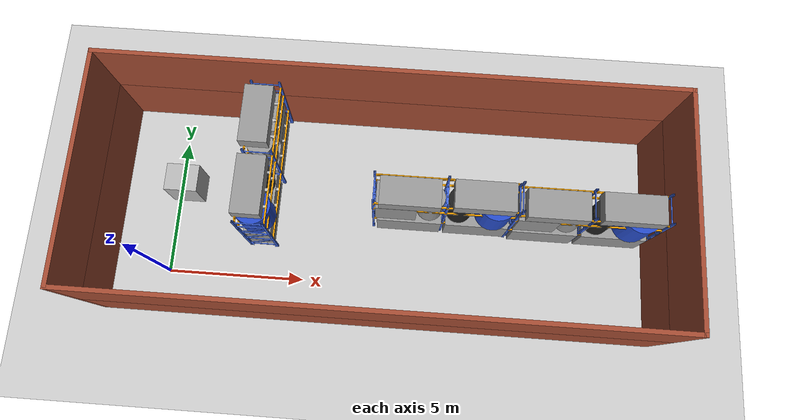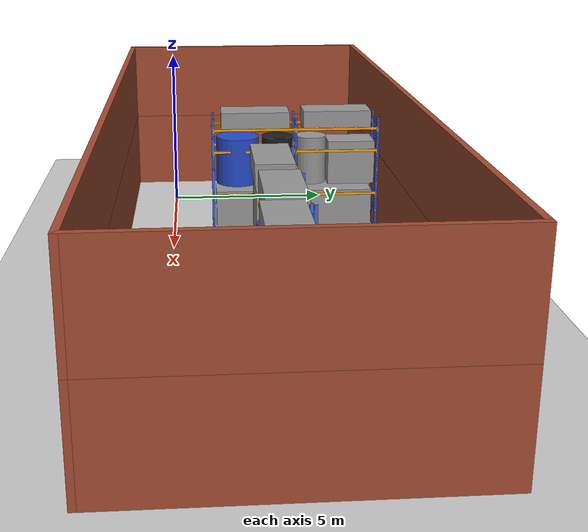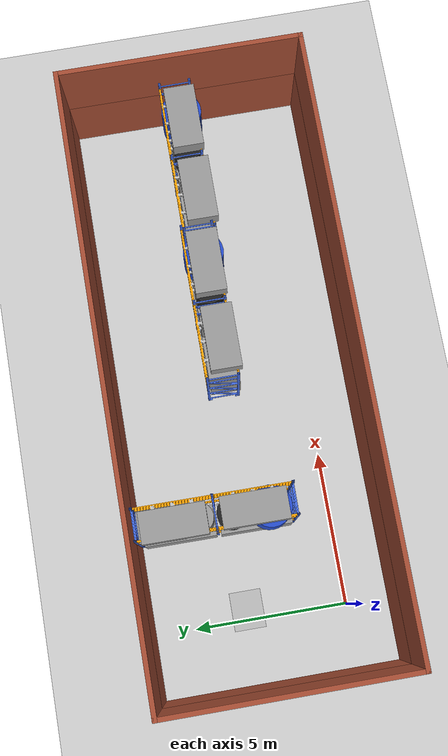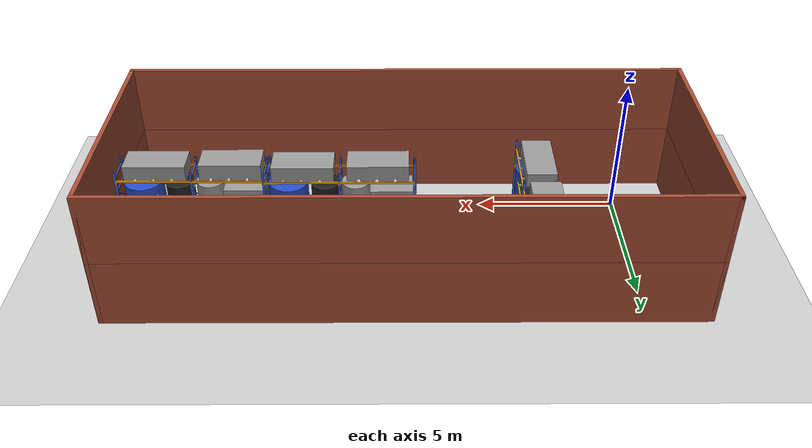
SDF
<sdf version="1.6">
 <world name="default">
  <light name="sun" type="directional">
   <pose>0 0 10 0 -0 0</pose>
   <diffuse>0.8 0.8 0.8 1</diffuse>
   <specular>0.1 0.1 0.1 1</specular>
   <attenuation>
    <range>1000</range>
    <constant>0.9</constant>
    <linear>0.01</linear>
    <quadratic>0.001</quadratic>
   </attenuation>
   <direction>-0.5 0.5 -1</direction>
  </light>
  <model name="ground_plane">
   <static>1</static>
   <link name="link">
    <collision name="collision">
     <geometry><plane><normal>0 0 1</normal><size>100 100</size></plane></geometry>
     <surface><friction><ode><mu>100</mu><mu2>50</mu2></ode></friction></surface>
    </collision>
    <visual name="visual">
     <cast_shadows>0</cast_shadows>
     <geometry><plane><normal>0 0 1</normal><size>100 100</size></plane></geometry>
     <material>
      <script><uri>file://media/materials/scripts/gazebo.material</uri><name>Gazebo/Grey</name></script>
     </material>
    </visual>
   </link>
  </model>
  <gravity>0 0 -9.8</gravity>
  <magnetic_field>6e-06 2.3e-05 -4.2e-05</magnetic_field>
  <atmosphere type="adiabatic"/>
  <physics name="default_physics" default="0" type="ode">
   <max_step_size>0.001</max_step_size>
   <real_time_factor>1</real_time_factor>
   <real_time_update_rate>1000</real_time_update_rate>
  </physics>
  <scene><ambient>0.4 0.4 0.4 1</ambient><background>0.7 0.7 0.7 1</background><shadows>1</shadows></scene>
  <spherical_coordinates>
   <surface_model>EARTH_WGS84</surface_model>
   <latitude_deg>0</latitude_deg>
   <longitude_deg>0</longitude_deg>
   <elevation>0</elevation>
   <heading_deg>0</heading_deg>
  </spherical_coordinates>
  <model name="WarehouseSmall_1">
   <link name="Wall_0">
    <pose>0 3.925 0 0 -0 0</pose>
    <visual name="Wall_0_Visual">
     <pose>0 0 1.25 0 -0 0</pose>
     <geometry><box><size>20 0.15 2.5</size></box></geometry>
     <material>
      <script><uri>file://media/materials/scripts/gazebo.material</uri><name>Gazebo/Bricks</name></script>
      <ambient>1 1 1 1</ambient>
      <diffuse>1 1 1 1</diffuse>
      <specular>0.2 0.2 0.2 1</specular>
      <emissive>0 0 0 1</emissive>
     </material>
    </visual>
    <collision name="Wall_0_Collision">
     <pose>0 0 1.25 0 -0 0</pose>
     <geometry><box><size>20 0.15 2.5</size></box></geometry>
     <surface>
      <friction>
       <ode><mu>1</mu><mu2>1</mu2><fdir1>0 0 0</fdir1><slip1>0</slip1><slip2>0</slip2></ode>
       <torsional>
        <coefficient>1</coefficient>
        <patch_radius>0</patch_radius>
        <surface_radius>0</surface_radius>
        <use_patch_radius>1</use_patch_radius>
        <ode><slip>0</slip></ode>
       </torsional>
      </friction>
      <bounce><restitution_coefficient>0</restitution_coefficient><threshold>1e+06</threshold></bounce>
      <contact>
       <collide_without_contact>0</collide_without_contact>
       <collide_without_contact_bitmask>1</collide_without_contact_bitmask>
       <collide_bitmask>1</collide_bitmask>
       <ode>
        <soft_cfm>0</soft_cfm>
        <soft_erp>0.2</soft_erp>
        <kp>1e+13</kp>
        <kd>1</kd>
        <max_vel>0.01</max_vel>
        <min_depth>0</min_depth>
       </ode>
       <bullet>
        <split_impulse>1</split_impulse>
        <split_impulse_penetration_threshold>-0.01</split_impulse_penetration_threshold>
        <soft_cfm>0</soft_cfm>
        <soft_erp>0.2</soft_erp>
        <kp>1e+13</kp>
        <kd>1</kd>
       </bullet>
      </contact>
     </surface>
    </collision>
   </link>
   <link name="Wall_1">
    <pose>9.925 0 0 0 0 -1.5708</pose>
    <visual name="Wall_1_Visual">
     <pose>0 0 1.25 0 -0 0</pose>
     <geometry><box><size>8 0.15 2.5</size></box></geometry>
     <material>
      <script><uri>file://media/materials/scripts/gazebo.material</uri><name>Gazebo/Bricks</name></script>
      <ambient>1 1 1 1</ambient>
      <diffuse>1 1 1 1</diffuse>
      <specular>0.2 0.2 0.2 1</specular>
      <emissive>0 0 0 1</emissive>
     </material>
    </visual>
    <collision name="Wall_1_Collision">
     <pose>0 0 1.25 0 -0 0</pose>
     <geometry><box><size>8 0.15 2.5</size></box></geometry>
     <surface>
      <friction>
       <ode><mu>1</mu><mu2>1</mu2><fdir1>0 0 0</fdir1><slip1>0</slip1><slip2>0</slip2></ode>
       <torsional>
        <coefficient>1</coefficient>
        <patch_radius>0</patch_radius>
        <surface_radius>0</surface_radius>
        <use_patch_radius>1</use_patch_radius>
        <ode><slip>0</slip></ode>
       </torsional>
      </friction>
      <bounce><restitution_coefficient>0</restitution_coefficient><threshold>1e+06</threshold></bounce>
      <contact>
       <collide_without_contact>0</collide_without_contact>
       <collide_without_contact_bitmask>1</collide_without_contact_bitmask>
       <collide_bitmask>1</collide_bitmask>
       <ode>
        <soft_cfm>0</soft_cfm>
        <soft_erp>0.2</soft_erp>
        <kp>1e+13</kp>
        <kd>1</kd>
        <max_vel>0.01</max_vel>
        <min_depth>0</min_depth>
       </ode>
       <bullet>
        <split_impulse>1</split_impulse>
        <split_impulse_penetration_threshold>-0.01</split_impulse_penetration_threshold>
        <soft_cfm>0</soft_cfm>
        <soft_erp>0.2</soft_erp>
        <kp>1e+13</kp>
        <kd>1</kd>
       </bullet>
      </contact>
     </surface>
    </collision>
   </link>
   <link name="Wall_2">
    <pose>0 -3.925 0 0 -0 3.14159</pose>
    <visual name="Wall_2_Visual">
     <pose>0 0 1.25 0 -0 0</pose>
     <geometry><box><size>20 0.15 2.5</size></box></geometry>
     <material>
      <script><uri>file://media/materials/scripts/gazebo.material</uri><name>Gazebo/Bricks</name></script>
      <ambient>1 1 1 1</ambient>
      <diffuse>1 1 1 1</diffuse>
      <specular>0.2 0.2 0.2 1</specular>
      <emissive>0 0 0 1</emissive>
     </material>
    </visual>
    <collision name="Wall_2_Collision">
     <pose>0 0 1.25 0 -0 0</pose>
     <geometry><box><size>20 0.15 2.5</size></box></geometry>
     <surface>
      <friction>
       <ode><mu>1</mu><mu2>1</mu2><fdir1>0 0 0</fdir1><slip1>0</slip1><slip2>0</slip2></ode>
       <torsional>
        <coefficient>1</coefficient>
        <patch_radius>0</patch_radius>
        <surface_radius>0</surface_radius>
        <use_patch_radius>1</use_patch_radius>
        <ode><slip>0</slip></ode>
       </torsional>
      </friction>
      <bounce><restitution_coefficient>0</restitution_coefficient><threshold>1e+06</threshold></bounce>
      <contact>
       <collide_without_contact>0</collide_without_contact>
       <collide_without_contact_bitmask>1</collide_without_contact_bitmask>
       <collide_bitmask>1</collide_bitmask>
       <ode>
        <soft_cfm>0</soft_cfm>
        <soft_erp>0.2</soft_erp>
        <kp>1e+13</kp>
        <kd>1</kd>
        <max_vel>0.01</max_vel>
        <min_depth>0</min_depth>
       </ode>
       <bullet>
        <split_impulse>1</split_impulse>
        <split_impulse_penetration_threshold>-0.01</split_impulse_penetration_threshold>
        <soft_cfm>0</soft_cfm>
        <soft_erp>0.2</soft_erp>
        <kp>1e+13</kp>
        <kd>1</kd>
       </bullet>
      </contact>
     </surface>
    </collision>
   </link>
   <link name="Wall_3">
    <pose>-9.925 0 0 0 -0 1.5708</pose>
    <visual name="Wall_3_Visual">
     <pose>0 0 1.25 0 -0 0</pose>
     <geometry><box><size>8 0.15 2.5</size></box></geometry>
     <material>
      <script><uri>file://media/materials/scripts/gazebo.material</uri><name>Gazebo/Bricks</name></script>
      <ambient>1 1 1 1</ambient>
      <diffuse>1 1 1 1</diffuse>
      <specular>0.2 0.2 0.2 1</specular>
      <emissive>0 0 0 1</emissive>
     </material>
    </visual>
    <collision name="Wall_3_Collision">
     <pose>0 0 1.25 0 -0 0</pose>
     <geometry><box><size>8 0.15 2.5</size></box></geometry>
     <surface>
      <friction>
       <ode><mu>1</mu><mu2>1</mu2><fdir1>0 0 0</fdir1><slip1>0</slip1><slip2>0</slip2></ode>
       <torsional>
        <coefficient>1</coefficient>
        <patch_radius>0</patch_radius>
        <surface_radius>0</surface_radius>
        <use_patch_radius>1</use_patch_radius>
        <ode><slip>0</slip></ode>
       </torsional>
      </friction>
      <bounce><restitution_coefficient>0</restitution_coefficient><threshold>1e+06</threshold></bounce>
      <contact>
       <collide_without_contact>0</collide_without_contact>
       <collide_without_contact_bitmask>1</collide_without_contact_bitmask>
       <collide_bitmask>1</collide_bitmask>
       <ode>
        <soft_cfm>0</soft_cfm>
        <soft_erp>0.2</soft_erp>
        <kp>1e+13</kp>
        <kd>1</kd>
        <max_vel>0.01</max_vel>
        <min_depth>0</min_depth>
       </ode>
       <bullet>
        <split_impulse>1</split_impulse>
        <split_impulse_penetration_threshold>-0.01</split_impulse_penetration_threshold>
        <soft_cfm>0</soft_cfm>
        <soft_erp>0.2</soft_erp>
        <kp>1e+13</kp>
        <kd>1</kd>
       </bullet>
      </contact>
     </surface>
    </collision>
   </link>
   <link name="Wall_5">
    <pose>0 3.925 2.5 0 -0 0</pose>
    <visual name="Wall_5_Visual">
     <pose>0 0 1.25 0 -0 0</pose>
     <geometry><box><size>20 0.15 2.5</size></box></geometry>
     <material>
      <script><uri>file://media/materials/scripts/gazebo.material</uri><name>Gazebo/Bricks</name></script>
      <ambient>1 1 1 1</ambient>
      <diffuse>1 1 1 1</diffuse>
      <specular>0.2 0.2 0.2 1</specular>
      <emissive>0 0 0 1</emissive>
     </material>
    </visual>
    <collision name="Wall_5_Collision">
     <pose>0 0 1.25 0 -0 0</pose>
     <geometry><box><size>20 0.15 2.5</size></box></geometry>
     <surface>
      <friction>
       <ode><mu>1</mu><mu2>1</mu2><fdir1>0 0 0</fdir1><slip1>0</slip1><slip2>0</slip2></ode>
       <torsional>
        <coefficient>1</coefficient>
        <patch_radius>0</patch_radius>
        <surface_radius>0</surface_radius>
        <use_patch_radius>1</use_patch_radius>
        <ode><slip>0</slip></ode>
       </torsional>
      </friction>
      <bounce><restitution_coefficient>0</restitution_coefficient><threshold>1e+06</threshold></bounce>
      <contact>
       <collide_without_contact>0</collide_without_contact>
       <collide_without_contact_bitmask>1</collide_without_contact_bitmask>
       <collide_bitmask>1</collide_bitmask>
       <ode>
        <soft_cfm>0</soft_cfm>
        <soft_erp>0.2</soft_erp>
        <kp>1e+13</kp>
        <kd>1</kd>
        <max_vel>0.01</max_vel>
        <min_depth>0</min_depth>
       </ode>
       <bullet>
        <split_impulse>1</split_impulse>
        <split_impulse_penetration_threshold>-0.01</split_impulse_penetration_threshold>
        <soft_cfm>0</soft_cfm>
        <soft_erp>0.2</soft_erp>
        <kp>1e+13</kp>
        <kd>1</kd>
       </bullet>
      </contact>
     </surface>
    </collision>
   </link>
   <link name="Wall_6">
    <pose>9.925 0 2.5 0 0 -1.5708</pose>
    <visual name="Wall_6_Visual">
     <pose>0 0 1.25 0 -0 0</pose>
     <geometry><box><size>8 0.15 2.5</size></box></geometry>
     <material>
      <script><uri>file://media/materials/scripts/gazebo.material</uri><name>Gazebo/Bricks</name></script>
      <ambient>1 1 1 1</ambient>
      <diffuse>1 1 1 1</diffuse>
      <specular>0.2 0.2 0.2 1</specular>
      <emissive>0 0 0 1</emissive>
     </material>
    </visual>
    <collision name="Wall_6_Collision">
     <pose>0 0 1.25 0 -0 0</pose>
     <geometry><box><size>8 0.15 2.5</size></box></geometry>
     <surface>
      <friction>
       <ode><mu>1</mu><mu2>1</mu2><fdir1>0 0 0</fdir1><slip1>0</slip1><slip2>0</slip2></ode>
       <torsional>
        <coefficient>1</coefficient>
        <patch_radius>0</patch_radius>
        <surface_radius>0</surface_radius>
        <use_patch_radius>1</use_patch_radius>
        <ode><slip>0</slip></ode>
       </torsional>
      </friction>
      <bounce><restitution_coefficient>0</restitution_coefficient><threshold>1e+06</threshold></bounce>
      <contact>
       <collide_without_contact>0</collide_without_contact>
       <collide_without_contact_bitmask>1</collide_without_contact_bitmask>
       <collide_bitmask>1</collide_bitmask>
       <ode>
        <soft_cfm>0</soft_cfm>
        <soft_erp>0.2</soft_erp>
        <kp>1e+13</kp>
        <kd>1</kd>
        <max_vel>0.01</max_vel>
        <min_depth>0</min_depth>
       </ode>
       <bullet>
        <split_impulse>1</split_impulse>
        <split_impulse_penetration_threshold>-0.01</split_impulse_penetration_threshold>
        <soft_cfm>0</soft_cfm>
        <soft_erp>0.2</soft_erp>
        <kp>1e+13</kp>
        <kd>1</kd>
       </bullet>
      </contact>
     </surface>
    </collision>
   </link>
   <link name="Wall_7">
    <pose>0 -3.925 2.5 0 -0 3.14159</pose>
    <visual name="Wall_7_Visual">
     <pose>0 0 1.25 0 -0 0</pose>
     <geometry><box><size>20 0.15 2.5</size></box></geometry>
     <material>
      <script><uri>file://media/materials/scripts/gazebo.material</uri><name>Gazebo/Bricks</name></script>
      <ambient>1 1 1 1</ambient>
      <diffuse>1 1 1 1</diffuse>
      <specular>0.2 0.2 0.2 1</specular>
      <emissive>0 0 0 1</emissive>
     </material>
    </visual>
    <collision name="Wall_7_Collision">
     <pose>0 0 1.25 0 -0 0</pose>
     <geometry><box><size>20 0.15 2.5</size></box></geometry>
     <surface>
      <friction>
       <ode><mu>1</mu><mu2>1</mu2><fdir1>0 0 0</fdir1><slip1>0</slip1><slip2>0</slip2></ode>
       <torsional>
        <coefficient>1</coefficient>
        <patch_radius>0</patch_radius>
        <surface_radius>0</surface_radius>
        <use_patch_radius>1</use_patch_radius>
        <ode><slip>0</slip></ode>
       </torsional>
      </friction>
      <bounce><restitution_coefficient>0</restitution_coefficient><threshold>1e+06</threshold></bounce>
      <contact>
       <collide_without_contact>0</collide_without_contact>
       <collide_without_contact_bitmask>1</collide_without_contact_bitmask>
       <collide_bitmask>1</collide_bitmask>
       <ode>
        <soft_cfm>0</soft_cfm>
        <soft_erp>0.2</soft_erp>
        <kp>1e+13</kp>
        <kd>1</kd>
        <max_vel>0.01</max_vel>
        <min_depth>0</min_depth>
       </ode>
       <bullet>
        <split_impulse>1</split_impulse>
        <split_impulse_penetration_threshold>-0.01</split_impulse_penetration_threshold>
        <soft_cfm>0</soft_cfm>
        <soft_erp>0.2</soft_erp>
        <kp>1e+13</kp>
        <kd>1</kd>
       </bullet>
      </contact>
     </surface>
    </collision>
   </link>
   <link name="Wall_8">
    <pose>-9.925 0 2.5 0 -0 1.5708</pose>
    <visual name="Wall_8_Visual">
     <pose>0 0 1.25 0 -0 0</pose>
     <geometry><box><size>8 0.15 2.5</size></box></geometry>
     <material>
      <script><uri>file://media/materials/scripts/gazebo.material</uri><name>Gazebo/Bricks</name></script>
      <ambient>1 1 1 1</ambient>
      <diffuse>1 1 1 1</diffuse>
      <specular>0.2 0.2 0.2 1</specular>
      <emissive>0 0 0 1</emissive>
     </material>
    </visual>
    <collision name="Wall_8_Collision">
     <pose>0 0 1.25 0 -0 0</pose>
     <geometry><box><size>8 0.15 2.5</size></box></geometry>
     <surface>
      <friction>
       <ode><mu>1</mu><mu2>1</mu2><fdir1>0 0 0</fdir1><slip1>0</slip1><slip2>0</slip2></ode>
       <torsional>
        <coefficient>1</coefficient>
        <patch_radius>0</patch_radius>
        <surface_radius>0</surface_radius>
        <use_patch_radius>1</use_patch_radius>
        <ode><slip>0</slip></ode>
       </torsional>
      </friction>
      <bounce><restitution_coefficient>0</restitution_coefficient><threshold>1e+06</threshold></bounce>
      <contact>
       <collide_without_contact>0</collide_without_contact>
       <collide_without_contact_bitmask>1</collide_without_contact_bitmask>
       <collide_bitmask>1</collide_bitmask>
       <ode>
        <soft_cfm>0</soft_cfm>
        <soft_erp>0.2</soft_erp>
        <kp>1e+13</kp>
        <kd>1</kd>
        <max_vel>0.01</max_vel>
        <min_depth>0</min_depth>
       </ode>
       <bullet>
        <split_impulse>1</split_impulse>
        <split_impulse_penetration_threshold>-0.01</split_impulse_penetration_threshold>
        <soft_cfm>0</soft_cfm>
        <soft_erp>0.2</soft_erp>
        <kp>1e+13</kp>
        <kd>1</kd>
       </bullet>
      </contact>
     </surface>
    </collision>
   </link>
   <static>1</static>
   <pose>7.78461 2.46373 0 0 -0 0</pose>
  </model>
  <model name="Full_shelf">
   <link name="link">
    <gravity>0</gravity>
    <inertial>
     <mass>1</mass>
     <inertia><ixx>1</ixx><ixy>0</ixy><ixz>0</ixz><iyy>1</iyy><iyz>0</iyz><izz>1</izz></inertia>
    </inertial>
    <visual name="visual">
     <geometry><mesh><uri>model://shelves_high/meshes/shelves_high.dae</uri><scale>1 1 1</scale></mesh></geometry>
     <material><shader type="vertex"><normal_map>__default__</normal_map></shader></material>
    </visual>
    <collision name="collision">
     <geometry>
      <mesh>
       <uri>/home/kosmastsk/.gazebo/models/shelves_high/meshes/shelves_high_collision.dae</uri>
       <scale>1 1 1</scale>
      </mesh>
     </geometry>
     <surface>
      <friction>
       <ode><mu>1</mu><mu2>1</mu2><fdir1>0 0 0</fdir1><slip1>0</slip1><slip2>0</slip2></ode>
       <torsional>
        <coefficient>1</coefficient>
        <patch_radius>0</patch_radius>
        <surface_radius>0</surface_radius>
        <use_patch_radius>1</use_patch_radius>
        <ode><slip>0</slip></ode>
       </torsional>
      </friction>
      <bounce><restitution_coefficient>0</restitution_coefficient><threshold>1e+06</threshold></bounce>
      <contact>
       <collide_without_contact>0</collide_without_contact>
       <collide_without_contact_bitmask>1</collide_without_contact_bitmask>
       <collide_bitmask>1</collide_bitmask>
       <ode>
        <soft_cfm>0</soft_cfm>
        <soft_erp>0.2</soft_erp>
        <kp>1e+13</kp>
        <kd>1</kd>
        <max_vel>0.01</max_vel>
        <min_depth>0</min_depth>
       </ode>
       <bullet>
        <split_impulse>1</split_impulse>
        <split_impulse_penetration_threshold>-0.01</split_impulse_penetration_threshold>
        <soft_cfm>0</soft_cfm>
        <soft_erp>0.2</soft_erp>
        <kp>1e+13</kp>
        <kd>1</kd>
       </bullet>
      </contact>
     </surface>
    </collision>
   </link>
   <link name="link_0">
    <pose>-1.21806 -0.607758 0.705407 0 -0 0</pose>
    <inertial>
     <mass>3.0149</mass>
     <inertia><ixx>0.669682</ixx><ixy>0</ixy><ixz>0</ixz><iyy>1.78963</iyy><iyz>0</iyz><izz>1.62244</izz></inertia>
    </inertial>
    <gravity>0</gravity>
    <visual name="visual">
     <geometry><box><size>2.33617 1 1.29054</size></box></geometry>
     <material>
      <lighting>1</lighting>
      <script><uri>file://media/materials/scripts/gazebo.material</uri><name>Gazebo/Grey</name></script>
      <ambient>0.3 0.3 0.3 1</ambient>
      <diffuse>0.7 0.7 0.7 1</diffuse>
      <specular>0.01 0.01 0.01 1</specular>
      <emissive>0 0 0 1</emissive>
      <shader type="vertex"><normal_map>__default__</normal_map></shader>
     </material>
    </visual>
    <collision name="collision">
     <geometry><box><size>2.33617 1 1.29054</size></box></geometry>
     <surface>
      <friction>
       <ode><mu>1</mu><mu2>1</mu2><fdir1>0 0 0</fdir1><slip1>0</slip1><slip2>0</slip2></ode>
       <torsional>
        <coefficient>1</coefficient>
        <patch_radius>0</patch_radius>
        <surface_radius>0</surface_radius>
        <use_patch_radius>1</use_patch_radius>
        <ode><slip>0</slip></ode>
       </torsional>
      </friction>
      <bounce><restitution_coefficient>0</restitution_coefficient><threshold>1e+06</threshold></bounce>
      <contact>
       <collide_without_contact>0</collide_without_contact>
       <collide_without_contact_bitmask>1</collide_without_contact_bitmask>
       <collide_bitmask>1</collide_bitmask>
       <ode>
        <soft_cfm>0</soft_cfm>
        <soft_erp>0.2</soft_erp>
        <kp>1e+13</kp>
        <kd>1</kd>
        <max_vel>0.01</max_vel>
        <min_depth>0</min_depth>
       </ode>
       <bullet>
        <split_impulse>1</split_impulse>
        <split_impulse_penetration_threshold>-0.01</split_impulse_penetration_threshold>
        <soft_cfm>0</soft_cfm>
        <soft_erp>0.2</soft_erp>
        <kp>1e+13</kp>
        <kd>1</kd>
       </bullet>
      </contact>
     </surface>
    </collision>
   </link>
   <link name="link_0_clone">
    <pose>1.26342 -0.615799 0.705407 0 -0 0</pose>
    <inertial>
     <mass>3.0149</mass>
     <inertia><ixx>0.669682</ixx><ixy>0</ixy><ixz>0</ixz><iyy>1.78963</iyy><iyz>0</iyz><izz>1.62244</izz></inertia>
    </inertial>
    <gravity>0</gravity>
    <visual name="visual">
     <geometry><box><size>2.33617 1 1.29054</size></box></geometry>
     <material>
      <lighting>1</lighting>
      <script><uri>file://media/materials/scripts/gazebo.material</uri><name>Gazebo/Grey</name></script>
      <ambient>0.3 0.3 0.3 1</ambient>
      <diffuse>0.7 0.7 0.7 1</diffuse>
      <specular>0.01 0.01 0.01 1</specular>
      <emissive>0 0 0 1</emissive>
      <shader type="vertex"><normal_map>__default__</normal_map></shader>
     </material>
    </visual>
    <collision name="collision">
     <geometry><box><size>2.33617 1 1.29054</size></box></geometry>
     <surface>
      <friction>
       <ode><mu>1</mu><mu2>1</mu2><fdir1>0 0 0</fdir1><slip1>0</slip1><slip2>0</slip2></ode>
       <torsional>
        <coefficient>1</coefficient>
        <patch_radius>0</patch_radius>
        <surface_radius>0</surface_radius>
        <use_patch_radius>1</use_patch_radius>
        <ode><slip>0</slip></ode>
       </torsional>
      </friction>
      <bounce><restitution_coefficient>0</restitution_coefficient><threshold>1e+06</threshold></bounce>
      <contact>
       <collide_without_contact>0</collide_without_contact>
       <collide_without_contact_bitmask>1</collide_without_contact_bitmask>
       <collide_bitmask>1</collide_bitmask>
       <ode>
        <soft_cfm>0</soft_cfm>
        <soft_erp>0.2</soft_erp>
        <kp>1e+13</kp>
        <kd>1</kd>
        <max_vel>0.01</max_vel>
        <min_depth>0</min_depth>
       </ode>
       <bullet>
        <split_impulse>1</split_impulse>
        <split_impulse_penetration_threshold>-0.01</split_impulse_penetration_threshold>
        <soft_cfm>0</soft_cfm>
        <soft_erp>0.2</soft_erp>
        <kp>1e+13</kp>
        <kd>1</kd>
       </bullet>
      </contact>
     </surface>
    </collision>
   </link>
   <link name="link_1">
    <pose>-1.72249 -0.574926 2.23564 0 -0 0</pose>
    <inertial>
     <mass>1.9112</mass>
     <inertia>
      <ixx>0.442719</ixx>
      <ixy>0</ixy>
      <ixz>0</ixz>
      <iyy>0.610326</iyy>
      <iyz>0</iyz>
      <izz>0.48614</izz>
     </inertia>
    </inertial>
    <gravity>0</gravity>
    <visual name="visual">
     <geometry><box><size>1.43261 1 1.33407</size></box></geometry>
     <material>
      <lighting>1</lighting>
      <script><uri>file://media/materials/scripts/gazebo.material</uri><name>Gazebo/Grey</name></script>
      <ambient>0.3 0.3 0.3 1</ambient>
      <diffuse>0.7 0.7 0.7 1</diffuse>
      <specular>0.01 0.01 0.01 1</specular>
      <emissive>0 0 0 1</emissive>
      <shader type="vertex"><normal_map>__default__</normal_map></shader>
     </material>
    </visual>
    <collision name="collision">
     <geometry><box><size>1.43261 1 1.33407</size></box></geometry>
     <surface>
      <friction>
       <ode><mu>1</mu><mu2>1</mu2><fdir1>0 0 0</fdir1><slip1>0</slip1><slip2>0</slip2></ode>
       <torsional>
        <coefficient>1</coefficient>
        <patch_radius>0</patch_radius>
        <surface_radius>0</surface_radius>
        <use_patch_radius>1</use_patch_radius>
        <ode><slip>0</slip></ode>
       </torsional>
      </friction>
      <bounce><restitution_coefficient>0</restitution_coefficient><threshold>1e+06</threshold></bounce>
      <contact>
       <collide_without_contact>0</collide_without_contact>
       <collide_without_contact_bitmask>1</collide_without_contact_bitmask>
       <collide_bitmask>1</collide_bitmask>
       <ode>
        <soft_cfm>0</soft_cfm>
        <soft_erp>0.2</soft_erp>
        <kp>1e+13</kp>
        <kd>1</kd>
        <max_vel>0.01</max_vel>
        <min_depth>0</min_depth>
       </ode>
       <bullet>
        <split_impulse>1</split_impulse>
        <split_impulse_penetration_threshold>-0.01</split_impulse_penetration_threshold>
        <soft_cfm>0</soft_cfm>
        <soft_erp>0.2</soft_erp>
        <kp>1e+13</kp>
        <kd>1</kd>
       </bullet>
      </contact>
     </surface>
    </collision>
   </link>
   <link name="link_2">
    <pose>-0.517546 -0.576274 2.28472 0 -0 0</pose>
    <inertial>
     <mass>1.31196</mass>
     <inertia>
      <ixx>0.306625</ixx>
      <ixy>0</ixy>
      <ixz>0</ixz>
      <iyy>0.306625</iyy>
      <iyz>0</iyz>
      <izz>0.147406</izz>
     </inertia>
    </inertial>
    <gravity>0</gravity>
    <visual name="visual">
     <geometry><cylinder><radius>0.474045</radius><length>1.45961</length></cylinder></geometry>
     <material>
      <lighting>1</lighting>
      <script><uri>file://media/materials/scripts/gazebo.material</uri><name>Gazebo/Grey</name></script>
      <ambient>0.3 0.3 0.3 1</ambient>
      <diffuse>0.7 0.7 0.7 1</diffuse>
      <specular>0.01 0.01 0.01 1</specular>
      <emissive>0 0 0 1</emissive>
      <shader type="vertex"><normal_map>__default__</normal_map></shader>
     </material>
    </visual>
    <collision name="collision">
     <geometry><cylinder><radius>0.474045</radius><length>1.45961</length></cylinder></geometry>
     <surface>
      <friction>
       <ode><mu>1</mu><mu2>1</mu2><fdir1>0 0 0</fdir1><slip1>0</slip1><slip2>0</slip2></ode>
       <torsional>
        <coefficient>1</coefficient>
        <patch_radius>0</patch_radius>
        <surface_radius>0</surface_radius>
        <use_patch_radius>1</use_patch_radius>
        <ode><slip>0</slip></ode>
       </torsional>
      </friction>
      <bounce><restitution_coefficient>0</restitution_coefficient><threshold>1e+06</threshold></bounce>
      <contact>
       <collide_without_contact>0</collide_without_contact>
       <collide_without_contact_bitmask>1</collide_without_contact_bitmask>
       <collide_bitmask>1</collide_bitmask>
       <ode>
        <soft_cfm>0</soft_cfm>
        <soft_erp>0.2</soft_erp>
        <kp>1e+13</kp>
        <kd>1</kd>
        <max_vel>0.01</max_vel>
        <min_depth>0</min_depth>
       </ode>
       <bullet>
        <split_impulse>1</split_impulse>
        <split_impulse_penetration_threshold>-0.01</split_impulse_penetration_threshold>
        <soft_cfm>0</soft_cfm>
        <soft_erp>0.2</soft_erp>
        <kp>1e+13</kp>
        <kd>1</kd>
       </bullet>
      </contact>
     </surface>
    </collision>
   </link>
   <link name="link_2_clone">
    <pose>0.526936 -0.581711 2.28472 0 -0 0</pose>
    <inertial>
     <mass>1.31196</mass>
     <inertia>
      <ixx>0.306625</ixx>
      <ixy>0</ixy>
      <ixz>0</ixz>
      <iyy>0.306625</iyy>
      <iyz>0</iyz>
      <izz>0.147406</izz>
     </inertia>
    </inertial>
    <gravity>0</gravity>
    <visual name="visual">
     <geometry><cylinder><radius>0.474045</radius><length>1.45961</length></cylinder></geometry>
     <material>
      <lighting>1</lighting>
      <script><uri>file://media/materials/scripts/gazebo.material</uri><name>Gazebo/Black</name></script>
      <ambient>0.3 0.3 0.3 1</ambient>
      <diffuse>0.7 0.7 0.7 1</diffuse>
      <specular>0.01 0.01 0.01 1</specular>
      <emissive>0 0 0 1</emissive>
      <shader type="vertex"><normal_map>__default__</normal_map></shader>
     </material>
    </visual>
    <collision name="collision">
     <geometry><cylinder><radius>0.474045</radius><length>1.45961</length></cylinder></geometry>
     <surface>
      <friction>
       <ode><mu>1</mu><mu2>1</mu2><fdir1>0 0 0</fdir1><slip1>0</slip1><slip2>0</slip2></ode>
       <torsional>
        <coefficient>1</coefficient>
        <patch_radius>0</patch_radius>
        <surface_radius>0</surface_radius>
        <use_patch_radius>1</use_patch_radius>
        <ode><slip>0</slip></ode>
       </torsional>
      </friction>
      <bounce><restitution_coefficient>0</restitution_coefficient><threshold>1e+06</threshold></bounce>
      <contact>
       <collide_without_contact>0</collide_without_contact>
       <collide_without_contact_bitmask>1</collide_without_contact_bitmask>
       <collide_bitmask>1</collide_bitmask>
       <ode>
        <soft_cfm>0</soft_cfm>
        <soft_erp>0.2</soft_erp>
        <kp>1e+13</kp>
        <kd>1</kd>
        <max_vel>0.01</max_vel>
        <min_depth>0</min_depth>
       </ode>
       <bullet>
        <split_impulse>1</split_impulse>
        <split_impulse_penetration_threshold>-0.01</split_impulse_penetration_threshold>
        <soft_cfm>0</soft_cfm>
        <soft_erp>0.2</soft_erp>
        <kp>1e+13</kp>
        <kd>1</kd>
       </bullet>
      </contact>
     </surface>
    </collision>
   </link>
   <link name="link_2_clone_0">
    <pose>1.75429 -0.591645 2.28472 0 -0 0</pose>
    <inertial>
     <mass>2.53501</mass>
     <inertia>
      <ixx>0.725231</ixx>
      <ixy>0</ixy>
      <ixz>0</ixz>
      <iyy>0.725231</iyy>
      <iyz>0</iyz>
      <izz>0.550343</izz>
     </inertia>
    </inertial>
    <gravity>0</gravity>
    <visual name="visual">
     <geometry><cylinder><radius>0.658947</radius><length>1.45961</length></cylinder></geometry>
     <material>
      <lighting>1</lighting>
      <script><uri>file://media/materials/scripts/gazebo.material</uri><name>Gazebo/Blue</name></script>
      <ambient>0.3 0.3 0.3 1</ambient>
      <diffuse>0.7 0.7 0.7 1</diffuse>
      <specular>0.01 0.01 0.01 1</specular>
      <emissive>0 0 0 1</emissive>
      <shader type="vertex"><normal_map>__default__</normal_map></shader>
     </material>
    </visual>
    <collision name="collision">
     <geometry><cylinder><radius>0.658947</radius><length>1.45961</length></cylinder></geometry>
     <surface>
      <friction>
       <ode><mu>1</mu><mu2>1</mu2><fdir1>0 0 0</fdir1><slip1>0</slip1><slip2>0</slip2></ode>
       <torsional>
        <coefficient>1</coefficient>
        <patch_radius>0</patch_radius>
        <surface_radius>0</surface_radius>
        <use_patch_radius>1</use_patch_radius>
        <ode><slip>0</slip></ode>
       </torsional>
      </friction>
      <bounce><restitution_coefficient>0</restitution_coefficient><threshold>1e+06</threshold></bounce>
      <contact>
       <collide_without_contact>0</collide_without_contact>
       <collide_without_contact_bitmask>1</collide_without_contact_bitmask>
       <collide_bitmask>1</collide_bitmask>
       <ode>
        <soft_cfm>0</soft_cfm>
        <soft_erp>0.2</soft_erp>
        <kp>1e+13</kp>
        <kd>1</kd>
        <max_vel>0.01</max_vel>
        <min_depth>0</min_depth>
       </ode>
       <bullet>
        <split_impulse>1</split_impulse>
        <split_impulse_penetration_threshold>-0.01</split_impulse_penetration_threshold>
        <soft_cfm>0</soft_cfm>
        <soft_erp>0.2</soft_erp>
        <kp>1e+13</kp>
        <kd>1</kd>
       </bullet>
      </contact>
     </surface>
    </collision>
   </link>
   <link name="link_3">
    <pose>-1.28062 -0.665513 3.55602 0 -0 0</pose>
    <inertial>
     <mass>1.1657</mass>
     <inertia>
      <ixx>0.127836</ixx>
      <ixy>0</ixy>
      <ixz>0</ixz>
      <iyy>0.448459</iyy>
      <iyz>0</iyz>
      <izz>0.514907</izz>
     </inertia>
    </inertial>
    <gravity>0</gravity>
    <visual name="visual">
     <geometry><box><size>2.07377 1 0.562114</size></box></geometry>
     <material>
      <lighting>1</lighting>
      <script><uri>file://media/materials/scripts/gazebo.material</uri><name>Gazebo/Grey</name></script>
      <ambient>0.3 0.3 0.3 1</ambient>
      <diffuse>0.7 0.7 0.7 1</diffuse>
      <specular>0.01 0.01 0.01 1</specular>
      <emissive>0 0 0 1</emissive>
      <shader type="vertex"><normal_map>__default__</normal_map></shader>
     </material>
    </visual>
    <collision name="collision">
     <geometry><box><size>2.07377 1 0.562114</size></box></geometry>
     <surface>
      <friction>
       <ode><mu>1</mu><mu2>1</mu2><fdir1>0 0 0</fdir1><slip1>0</slip1><slip2>0</slip2></ode>
       <torsional>
        <coefficient>1</coefficient>
        <patch_radius>0</patch_radius>
        <surface_radius>0</surface_radius>
        <use_patch_radius>1</use_patch_radius>
        <ode><slip>0</slip></ode>
       </torsional>
      </friction>
      <bounce><restitution_coefficient>0</restitution_coefficient><threshold>1e+06</threshold></bounce>
      <contact>
       <collide_without_contact>0</collide_without_contact>
       <collide_without_contact_bitmask>1</collide_without_contact_bitmask>
       <collide_bitmask>1</collide_bitmask>
       <ode>
        <soft_cfm>0</soft_cfm>
        <soft_erp>0.2</soft_erp>
        <kp>1e+13</kp>
        <kd>1</kd>
        <max_vel>0.01</max_vel>
        <min_depth>0</min_depth>
       </ode>
       <bullet>
        <split_impulse>1</split_impulse>
        <split_impulse_penetration_threshold>-0.01</split_impulse_penetration_threshold>
        <soft_cfm>0</soft_cfm>
        <soft_erp>0.2</soft_erp>
        <kp>1e+13</kp>
        <kd>1</kd>
       </bullet>
      </contact>
     </surface>
    </collision>
   </link>
   <link name="link_3_clone">
    <pose>1.22598 -0.613311 3.54121 0 -0 0</pose>
    <inertial>
     <mass>1.1657</mass>
     <inertia>
      <ixx>0.127836</ixx>
      <ixy>0</ixy>
      <ixz>0</ixz>
      <iyy>0.448459</iyy>
      <iyz>0</iyz>
      <izz>0.514907</izz>
     </inertia>
    </inertial>
    <gravity>0</gravity>
    <visual name="visual">
     <geometry><box><size>2.07377 1 0.562114</size></box></geometry>
     <material>
      <lighting>1</lighting>
      <script><uri>file://media/materials/scripts/gazebo.material</uri><name>Gazebo/Grey</name></script>
      <ambient>0.3 0.3 0.3 1</ambient>
      <diffuse>0.7 0.7 0.7 1</diffuse>
      <specular>0.01 0.01 0.01 1</specular>
      <emissive>0 0 0 1</emissive>
      <shader type="vertex"><normal_map>__default__</normal_map></shader>
     </material>
    </visual>
    <collision name="collision">
     <geometry><box><size>2.07377 1 0.562114</size></box></geometry>
     <surface>
      <friction>
       <ode><mu>1</mu><mu2>1</mu2><fdir1>0 0 0</fdir1><slip1>0</slip1><slip2>0</slip2></ode>
       <torsional>
        <coefficient>1</coefficient>
        <patch_radius>0</patch_radius>
        <surface_radius>0</surface_radius>
        <use_patch_radius>1</use_patch_radius>
        <ode><slip>0</slip></ode>
       </torsional>
      </friction>
      <bounce><restitution_coefficient>0</restitution_coefficient><threshold>1e+06</threshold></bounce>
      <contact>
       <collide_without_contact>0</collide_without_contact>
       <collide_without_contact_bitmask>1</collide_without_contact_bitmask>
       <collide_bitmask>1</collide_bitmask>
       <ode>
        <soft_cfm>0</soft_cfm>
        <soft_erp>0.2</soft_erp>
        <kp>1e+13</kp>
        <kd>1</kd>
        <max_vel>0.01</max_vel>
        <min_depth>0</min_depth>
       </ode>
       <bullet>
        <split_impulse>1</split_impulse>
        <split_impulse_penetration_threshold>-0.01</split_impulse_penetration_threshold>
        <soft_cfm>0</soft_cfm>
        <soft_erp>0.2</soft_erp>
        <kp>1e+13</kp>
        <kd>1</kd>
       </bullet>
      </contact>
     </surface>
    </collision>
   </link>
   <static>1</static>
   <pose>14.9388 3.2209 0 0 -0 0</pose>
  </model>
  <model name="Full_shelf_0">
   <link name="link">
    <gravity>0</gravity>
    <inertial>
     <mass>1</mass>
     <inertia><ixx>1</ixx><ixy>0</ixy><ixz>0</ixz><iyy>1</iyy><iyz>0</iyz><izz>1</izz></inertia>
    </inertial>
    <visual name="visual">
     <geometry><mesh><uri>model://shelves_high/meshes/shelves_high.dae</uri><scale>1 1 1</scale></mesh></geometry>
     <material><shader type="vertex"><normal_map>__default__</normal_map></shader></material>
    </visual>
    <collision name="collision">
     <geometry>
      <mesh>
       <uri>/home/kosmastsk/.gazebo/models/shelves_high/meshes/shelves_high_collision.dae</uri>
       <scale>1 1 1</scale>
      </mesh>
     </geometry>
     <surface>
      <friction>
       <ode><mu>1</mu><mu2>1</mu2><fdir1>0 0 0</fdir1><slip1>0</slip1><slip2>0</slip2></ode>
       <torsional>
        <coefficient>1</coefficient>
        <patch_radius>0</patch_radius>
        <surface_radius>0</surface_radius>
        <use_patch_radius>1</use_patch_radius>
        <ode><slip>0</slip></ode>
       </torsional>
      </friction>
      <bounce><restitution_coefficient>0</restitution_coefficient><threshold>1e+06</threshold></bounce>
      <contact>
       <collide_without_contact>0</collide_without_contact>
       <collide_without_contact_bitmask>1</collide_without_contact_bitmask>
       <collide_bitmask>1</collide_bitmask>
       <ode>
        <soft_cfm>0</soft_cfm>
        <soft_erp>0.2</soft_erp>
        <kp>1e+13</kp>
        <kd>1</kd>
        <max_vel>0.01</max_vel>
        <min_depth>0</min_depth>
       </ode>
       <bullet>
        <split_impulse>1</split_impulse>
        <split_impulse_penetration_threshold>-0.01</split_impulse_penetration_threshold>
        <soft_cfm>0</soft_cfm>
        <soft_erp>0.2</soft_erp>
        <kp>1e+13</kp>
        <kd>1</kd>
       </bullet>
      </contact>
     </surface>
    </collision>
   </link>
   <link name="link_0">
    <pose>-1.21806 -0.607758 0.705407 0 -0 0</pose>
    <inertial>
     <mass>3.0149</mass>
     <inertia><ixx>0.669682</ixx><ixy>0</ixy><ixz>0</ixz><iyy>1.78963</iyy><iyz>0</iyz><izz>1.62244</izz></inertia>
    </inertial>
    <gravity>0</gravity>
    <visual name="visual">
     <geometry><box><size>2.33617 1 1.29054</size></box></geometry>
     <material>
      <lighting>1</lighting>
      <script><uri>file://media/materials/scripts/gazebo.material</uri><name>Gazebo/Grey</name></script>
      <ambient>0.3 0.3 0.3 1</ambient>
      <diffuse>0.7 0.7 0.7 1</diffuse>
      <specular>0.01 0.01 0.01 1</specular>
      <emissive>0 0 0 1</emissive>
      <shader type="vertex"><normal_map>__default__</normal_map></shader>
     </material>
    </visual>
    <collision name="collision">
     <geometry><box><size>2.33617 1 1.29054</size></box></geometry>
     <surface>
      <friction>
       <ode><mu>1</mu><mu2>1</mu2><fdir1>0 0 0</fdir1><slip1>0</slip1><slip2>0</slip2></ode>
       <torsional>
        <coefficient>1</coefficient>
        <patch_radius>0</patch_radius>
        <surface_radius>0</surface_radius>
        <use_patch_radius>1</use_patch_radius>
        <ode><slip>0</slip></ode>
       </torsional>
      </friction>
      <bounce><restitution_coefficient>0</restitution_coefficient><threshold>1e+06</threshold></bounce>
      <contact>
       <collide_without_contact>0</collide_without_contact>
       <collide_without_contact_bitmask>1</collide_without_contact_bitmask>
       <collide_bitmask>1</collide_bitmask>
       <ode>
        <soft_cfm>0</soft_cfm>
        <soft_erp>0.2</soft_erp>
        <kp>1e+13</kp>
        <kd>1</kd>
        <max_vel>0.01</max_vel>
        <min_depth>0</min_depth>
       </ode>
       <bullet>
        <split_impulse>1</split_impulse>
        <split_impulse_penetration_threshold>-0.01</split_impulse_penetration_threshold>
        <soft_cfm>0</soft_cfm>
        <soft_erp>0.2</soft_erp>
        <kp>1e+13</kp>
        <kd>1</kd>
       </bullet>
      </contact>
     </surface>
    </collision>
   </link>
   <link name="link_0_clone">
    <pose>1.26342 -0.615799 0.705407 0 -0 0</pose>
    <inertial>
     <mass>3.0149</mass>
     <inertia><ixx>0.669682</ixx><ixy>0</ixy><ixz>0</ixz><iyy>1.78963</iyy><iyz>0</iyz><izz>1.62244</izz></inertia>
    </inertial>
    <gravity>0</gravity>
    <visual name="visual">
     <geometry><box><size>2.33617 1 1.29054</size></box></geometry>
     <material>
      <lighting>1</lighting>
      <script><uri>file://media/materials/scripts/gazebo.material</uri><name>Gazebo/Grey</name></script>
      <ambient>0.3 0.3 0.3 1</ambient>
      <diffuse>0.7 0.7 0.7 1</diffuse>
      <specular>0.01 0.01 0.01 1</specular>
      <emissive>0 0 0 1</emissive>
      <shader type="vertex"><normal_map>__default__</normal_map></shader>
     </material>
    </visual>
    <collision name="collision">
     <geometry><box><size>2.33617 1 1.29054</size></box></geometry>
     <surface>
      <friction>
       <ode><mu>1</mu><mu2>1</mu2><fdir1>0 0 0</fdir1><slip1>0</slip1><slip2>0</slip2></ode>
       <torsional>
        <coefficient>1</coefficient>
        <patch_radius>0</patch_radius>
        <surface_radius>0</surface_radius>
        <use_patch_radius>1</use_patch_radius>
        <ode><slip>0</slip></ode>
       </torsional>
      </friction>
      <bounce><restitution_coefficient>0</restitution_coefficient><threshold>1e+06</threshold></bounce>
      <contact>
       <collide_without_contact>0</collide_without_contact>
       <collide_without_contact_bitmask>1</collide_without_contact_bitmask>
       <collide_bitmask>1</collide_bitmask>
       <ode>
        <soft_cfm>0</soft_cfm>
        <soft_erp>0.2</soft_erp>
        <kp>1e+13</kp>
        <kd>1</kd>
        <max_vel>0.01</max_vel>
        <min_depth>0</min_depth>
       </ode>
       <bullet>
        <split_impulse>1</split_impulse>
        <split_impulse_penetration_threshold>-0.01</split_impulse_penetration_threshold>
        <soft_cfm>0</soft_cfm>
        <soft_erp>0.2</soft_erp>
        <kp>1e+13</kp>
        <kd>1</kd>
       </bullet>
      </contact>
     </surface>
    </collision>
   </link>
   <link name="link_1">
    <pose>-1.72249 -0.574926 2.23564 0 -0 0</pose>
    <inertial>
     <mass>1.9112</mass>
     <inertia>
      <ixx>0.442719</ixx>
      <ixy>0</ixy>
      <ixz>0</ixz>
      <iyy>0.610326</iyy>
      <iyz>0</iyz>
      <izz>0.48614</izz>
     </inertia>
    </inertial>
    <gravity>0</gravity>
    <visual name="visual">
     <geometry><box><size>1.43261 1 1.33407</size></box></geometry>
     <material>
      <lighting>1</lighting>
      <script><uri>file://media/materials/scripts/gazebo.material</uri><name>Gazebo/Grey</name></script>
      <ambient>0.3 0.3 0.3 1</ambient>
      <diffuse>0.7 0.7 0.7 1</diffuse>
      <specular>0.01 0.01 0.01 1</specular>
      <emissive>0 0 0 1</emissive>
      <shader type="vertex"><normal_map>__default__</normal_map></shader>
     </material>
    </visual>
    <collision name="collision">
     <geometry><box><size>1.43261 1 1.33407</size></box></geometry>
     <surface>
      <friction>
       <ode><mu>1</mu><mu2>1</mu2><fdir1>0 0 0</fdir1><slip1>0</slip1><slip2>0</slip2></ode>
       <torsional>
        <coefficient>1</coefficient>
        <patch_radius>0</patch_radius>
        <surface_radius>0</surface_radius>
        <use_patch_radius>1</use_patch_radius>
        <ode><slip>0</slip></ode>
       </torsional>
      </friction>
      <bounce><restitution_coefficient>0</restitution_coefficient><threshold>1e+06</threshold></bounce>
      <contact>
       <collide_without_contact>0</collide_without_contact>
       <collide_without_contact_bitmask>1</collide_without_contact_bitmask>
       <collide_bitmask>1</collide_bitmask>
       <ode>
        <soft_cfm>0</soft_cfm>
        <soft_erp>0.2</soft_erp>
        <kp>1e+13</kp>
        <kd>1</kd>
        <max_vel>0.01</max_vel>
        <min_depth>0</min_depth>
       </ode>
       <bullet>
        <split_impulse>1</split_impulse>
        <split_impulse_penetration_threshold>-0.01</split_impulse_penetration_threshold>
        <soft_cfm>0</soft_cfm>
        <soft_erp>0.2</soft_erp>
        <kp>1e+13</kp>
        <kd>1</kd>
       </bullet>
      </contact>
     </surface>
    </collision>
   </link>
   <link name="link_2">
    <pose>-0.517546 -0.576274 2.28472 0 -0 0</pose>
    <inertial>
     <mass>1.31196</mass>
     <inertia>
      <ixx>0.306625</ixx>
      <ixy>0</ixy>
      <ixz>0</ixz>
      <iyy>0.306625</iyy>
      <iyz>0</iyz>
      <izz>0.147406</izz>
     </inertia>
    </inertial>
    <gravity>0</gravity>
    <visual name="visual">
     <geometry><cylinder><radius>0.474045</radius><length>1.45961</length></cylinder></geometry>
     <material>
      <lighting>1</lighting>
      <script><uri>file://media/materials/scripts/gazebo.material</uri><name>Gazebo/Grey</name></script>
      <ambient>0.3 0.3 0.3 1</ambient>
      <diffuse>0.7 0.7 0.7 1</diffuse>
      <specular>0.01 0.01 0.01 1</specular>
      <emissive>0 0 0 1</emissive>
      <shader type="vertex"><normal_map>__default__</normal_map></shader>
     </material>
    </visual>
    <collision name="collision">
     <geometry><cylinder><radius>0.474045</radius><length>1.45961</length></cylinder></geometry>
     <surface>
      <friction>
       <ode><mu>1</mu><mu2>1</mu2><fdir1>0 0 0</fdir1><slip1>0</slip1><slip2>0</slip2></ode>
       <torsional>
        <coefficient>1</coefficient>
        <patch_radius>0</patch_radius>
        <surface_radius>0</surface_radius>
        <use_patch_radius>1</use_patch_radius>
        <ode><slip>0</slip></ode>
       </torsional>
      </friction>
      <bounce><restitution_coefficient>0</restitution_coefficient><threshold>1e+06</threshold></bounce>
      <contact>
       <collide_without_contact>0</collide_without_contact>
       <collide_without_contact_bitmask>1</collide_without_contact_bitmask>
       <collide_bitmask>1</collide_bitmask>
       <ode>
        <soft_cfm>0</soft_cfm>
        <soft_erp>0.2</soft_erp>
        <kp>1e+13</kp>
        <kd>1</kd>
        <max_vel>0.01</max_vel>
        <min_depth>0</min_depth>
       </ode>
       <bullet>
        <split_impulse>1</split_impulse>
        <split_impulse_penetration_threshold>-0.01</split_impulse_penetration_threshold>
        <soft_cfm>0</soft_cfm>
        <soft_erp>0.2</soft_erp>
        <kp>1e+13</kp>
        <kd>1</kd>
       </bullet>
      </contact>
     </surface>
    </collision>
   </link>
   <link name="link_2_clone">
    <pose>0.526936 -0.581711 2.28472 0 -0 0</pose>
    <inertial>
     <mass>1.31196</mass>
     <inertia>
      <ixx>0.306625</ixx>
      <ixy>0</ixy>
      <ixz>0</ixz>
      <iyy>0.306625</iyy>
      <iyz>0</iyz>
      <izz>0.147406</izz>
     </inertia>
    </inertial>
    <gravity>0</gravity>
    <visual name="visual">
     <geometry><cylinder><radius>0.474045</radius><length>1.45961</length></cylinder></geometry>
     <material>
      <lighting>1</lighting>
      <script><uri>file://media/materials/scripts/gazebo.material</uri><name>Gazebo/Black</name></script>
      <ambient>0.3 0.3 0.3 1</ambient>
      <diffuse>0.7 0.7 0.7 1</diffuse>
      <specular>0.01 0.01 0.01 1</specular>
      <emissive>0 0 0 1</emissive>
      <shader type="vertex"><normal_map>__default__</normal_map></shader>
     </material>
    </visual>
    <collision name="collision">
     <geometry><cylinder><radius>0.474045</radius><length>1.45961</length></cylinder></geometry>
     <surface>
      <friction>
       <ode><mu>1</mu><mu2>1</mu2><fdir1>0 0 0</fdir1><slip1>0</slip1><slip2>0</slip2></ode>
       <torsional>
        <coefficient>1</coefficient>
        <patch_radius>0</patch_radius>
        <surface_radius>0</surface_radius>
        <use_patch_radius>1</use_patch_radius>
        <ode><slip>0</slip></ode>
       </torsional>
      </friction>
      <bounce><restitution_coefficient>0</restitution_coefficient><threshold>1e+06</threshold></bounce>
      <contact>
       <collide_without_contact>0</collide_without_contact>
       <collide_without_contact_bitmask>1</collide_without_contact_bitmask>
       <collide_bitmask>1</collide_bitmask>
       <ode>
        <soft_cfm>0</soft_cfm>
        <soft_erp>0.2</soft_erp>
        <kp>1e+13</kp>
        <kd>1</kd>
        <max_vel>0.01</max_vel>
        <min_depth>0</min_depth>
       </ode>
       <bullet>
        <split_impulse>1</split_impulse>
        <split_impulse_penetration_threshold>-0.01</split_impulse_penetration_threshold>
        <soft_cfm>0</soft_cfm>
        <soft_erp>0.2</soft_erp>
        <kp>1e+13</kp>
        <kd>1</kd>
       </bullet>
      </contact>
     </surface>
    </collision>
   </link>
   <link name="link_2_clone_0">
    <pose>1.75429 -0.591645 2.28472 0 -0 0</pose>
    <inertial>
     <mass>2.53501</mass>
     <inertia>
      <ixx>0.725231</ixx>
      <ixy>0</ixy>
      <ixz>0</ixz>
      <iyy>0.725231</iyy>
      <iyz>0</iyz>
      <izz>0.550343</izz>
     </inertia>
    </inertial>
    <gravity>0</gravity>
    <visual name="visual">
     <geometry><cylinder><radius>0.658947</radius><length>1.45961</length></cylinder></geometry>
     <material>
      <lighting>1</lighting>
      <script><uri>file://media/materials/scripts/gazebo.material</uri><name>Gazebo/Blue</name></script>
      <ambient>0.3 0.3 0.3 1</ambient>
      <diffuse>0.7 0.7 0.7 1</diffuse>
      <specular>0.01 0.01 0.01 1</specular>
      <emissive>0 0 0 1</emissive>
      <shader type="vertex"><normal_map>__default__</normal_map></shader>
     </material>
    </visual>
    <collision name="collision">
     <geometry><cylinder><radius>0.658947</radius><length>1.45961</length></cylinder></geometry>
     <surface>
      <friction>
       <ode><mu>1</mu><mu2>1</mu2><fdir1>0 0 0</fdir1><slip1>0</slip1><slip2>0</slip2></ode>
       <torsional>
        <coefficient>1</coefficient>
        <patch_radius>0</patch_radius>
        <surface_radius>0</surface_radius>
        <use_patch_radius>1</use_patch_radius>
        <ode><slip>0</slip></ode>
       </torsional>
      </friction>
      <bounce><restitution_coefficient>0</restitution_coefficient><threshold>1e+06</threshold></bounce>
      <contact>
       <collide_without_contact>0</collide_without_contact>
       <collide_without_contact_bitmask>1</collide_without_contact_bitmask>
       <collide_bitmask>1</collide_bitmask>
       <ode>
        <soft_cfm>0</soft_cfm>
        <soft_erp>0.2</soft_erp>
        <kp>1e+13</kp>
        <kd>1</kd>
        <max_vel>0.01</max_vel>
        <min_depth>0</min_depth>
       </ode>
       <bullet>
        <split_impulse>1</split_impulse>
        <split_impulse_penetration_threshold>-0.01</split_impulse_penetration_threshold>
        <soft_cfm>0</soft_cfm>
        <soft_erp>0.2</soft_erp>
        <kp>1e+13</kp>
        <kd>1</kd>
       </bullet>
      </contact>
     </surface>
    </collision>
   </link>
   <link name="link_3">
    <pose>-1.28062 -0.665513 3.55602 0 -0 0</pose>
    <inertial>
     <mass>1.1657</mass>
     <inertia>
      <ixx>0.127836</ixx>
      <ixy>0</ixy>
      <ixz>0</ixz>
      <iyy>0.448459</iyy>
      <iyz>0</iyz>
      <izz>0.514907</izz>
     </inertia>
    </inertial>
    <gravity>0</gravity>
    <visual name="visual">
     <geometry><box><size>2.07377 1 0.562114</size></box></geometry>
     <material>
      <lighting>1</lighting>
      <script><uri>file://media/materials/scripts/gazebo.material</uri><name>Gazebo/Grey</name></script>
      <ambient>0.3 0.3 0.3 1</ambient>
      <diffuse>0.7 0.7 0.7 1</diffuse>
      <specular>0.01 0.01 0.01 1</specular>
      <emissive>0 0 0 1</emissive>
      <shader type="vertex"><normal_map>__default__</normal_map></shader>
     </material>
    </visual>
    <collision name="collision">
     <geometry><box><size>2.07377 1 0.562114</size></box></geometry>
     <surface>
      <friction>
       <ode><mu>1</mu><mu2>1</mu2><fdir1>0 0 0</fdir1><slip1>0</slip1><slip2>0</slip2></ode>
       <torsional>
        <coefficient>1</coefficient>
        <patch_radius>0</patch_radius>
        <surface_radius>0</surface_radius>
        <use_patch_radius>1</use_patch_radius>
        <ode><slip>0</slip></ode>
       </torsional>
      </friction>
      <bounce><restitution_coefficient>0</restitution_coefficient><threshold>1e+06</threshold></bounce>
      <contact>
       <collide_without_contact>0</collide_without_contact>
       <collide_without_contact_bitmask>1</collide_without_contact_bitmask>
       <collide_bitmask>1</collide_bitmask>
       <ode>
        <soft_cfm>0</soft_cfm>
        <soft_erp>0.2</soft_erp>
        <kp>1e+13</kp>
        <kd>1</kd>
        <max_vel>0.01</max_vel>
        <min_depth>0</min_depth>
       </ode>
       <bullet>
        <split_impulse>1</split_impulse>
        <split_impulse_penetration_threshold>-0.01</split_impulse_penetration_threshold>
        <soft_cfm>0</soft_cfm>
        <soft_erp>0.2</soft_erp>
        <kp>1e+13</kp>
        <kd>1</kd>
       </bullet>
      </contact>
     </surface>
    </collision>
   </link>
   <link name="link_3_clone">
    <pose>1.22598 -0.613311 3.54121 0 -0 0</pose>
    <inertial>
     <mass>1.1657</mass>
     <inertia>
      <ixx>0.127836</ixx>
      <ixy>0</ixy>
      <ixz>0</ixz>
      <iyy>0.448459</iyy>
      <iyz>0</iyz>
      <izz>0.514907</izz>
     </inertia>
    </inertial>
    <gravity>0</gravity>
    <visual name="visual">
     <geometry><box><size>2.07377 1 0.562114</size></box></geometry>
     <material>
      <lighting>1</lighting>
      <script><uri>file://media/materials/scripts/gazebo.material</uri><name>Gazebo/Grey</name></script>
      <ambient>0.3 0.3 0.3 1</ambient>
      <diffuse>0.7 0.7 0.7 1</diffuse>
      <specular>0.01 0.01 0.01 1</specular>
      <emissive>0 0 0 1</emissive>
      <shader type="vertex"><normal_map>__default__</normal_map></shader>
     </material>
    </visual>
    <collision name="collision">
     <geometry><box><size>2.07377 1 0.562114</size></box></geometry>
     <surface>
      <friction>
       <ode><mu>1</mu><mu2>1</mu2><fdir1>0 0 0</fdir1><slip1>0</slip1><slip2>0</slip2></ode>
       <torsional>
        <coefficient>1</coefficient>
        <patch_radius>0</patch_radius>
        <surface_radius>0</surface_radius>
        <use_patch_radius>1</use_patch_radius>
        <ode><slip>0</slip></ode>
       </torsional>
      </friction>
      <bounce><restitution_coefficient>0</restitution_coefficient><threshold>1e+06</threshold></bounce>
      <contact>
       <collide_without_contact>0</collide_without_contact>
       <collide_without_contact_bitmask>1</collide_without_contact_bitmask>
       <collide_bitmask>1</collide_bitmask>
       <ode>
        <soft_cfm>0</soft_cfm>
        <soft_erp>0.2</soft_erp>
        <kp>1e+13</kp>
        <kd>1</kd>
        <max_vel>0.01</max_vel>
        <min_depth>0</min_depth>
       </ode>
       <bullet>
        <split_impulse>1</split_impulse>
        <split_impulse_penetration_threshold>-0.01</split_impulse_penetration_threshold>
        <soft_cfm>0</soft_cfm>
        <soft_erp>0.2</soft_erp>
        <kp>1e+13</kp>
        <kd>1</kd>
       </bullet>
      </contact>
     </surface>
    </collision>
   </link>
   <static>1</static>
   <pose>10.013 3.30547 0 0 -0 0</pose>
  </model>
  <model name="Full_shelf_1">
   <link name="link">
    <gravity>0</gravity>
    <inertial>
     <mass>1</mass>
     <inertia><ixx>1</ixx><ixy>0</ixy><ixz>0</ixz><iyy>1</iyy><iyz>0</iyz><izz>1</izz></inertia>
    </inertial>
    <visual name="visual">
     <geometry><mesh><uri>model://shelves_high/meshes/shelves_high.dae</uri><scale>1 1 1</scale></mesh></geometry>
     <material><shader type="vertex"><normal_map>__default__</normal_map></shader></material>
    </visual>
    <collision name="collision">
     <geometry>
      <mesh>
       <uri>/home/kosmastsk/.gazebo/models/shelves_high/meshes/shelves_high_collision.dae</uri>
       <scale>1 1 1</scale>
      </mesh>
     </geometry>
     <surface>
      <friction>
       <ode><mu>1</mu><mu2>1</mu2><fdir1>0 0 0</fdir1><slip1>0</slip1><slip2>0</slip2></ode>
       <torsional>
        <coefficient>1</coefficient>
        <patch_radius>0</patch_radius>
        <surface_radius>0</surface_radius>
        <use_patch_radius>1</use_patch_radius>
        <ode><slip>0</slip></ode>
       </torsional>
      </friction>
      <bounce><restitution_coefficient>0</restitution_coefficient><threshold>1e+06</threshold></bounce>
      <contact>
       <collide_without_contact>0</collide_without_contact>
       <collide_without_contact_bitmask>1</collide_without_contact_bitmask>
       <collide_bitmask>1</collide_bitmask>
       <ode>
        <soft_cfm>0</soft_cfm>
        <soft_erp>0.2</soft_erp>
        <kp>1e+13</kp>
        <kd>1</kd>
        <max_vel>0.01</max_vel>
        <min_depth>0</min_depth>
       </ode>
       <bullet>
        <split_impulse>1</split_impulse>
        <split_impulse_penetration_threshold>-0.01</split_impulse_penetration_threshold>
        <soft_cfm>0</soft_cfm>
        <soft_erp>0.2</soft_erp>
        <kp>1e+13</kp>
        <kd>1</kd>
       </bullet>
      </contact>
     </surface>
    </collision>
   </link>
   <link name="link_0">
    <pose>-1.21806 -0.607758 0.705407 0 -0 0</pose>
    <inertial>
     <mass>3.0149</mass>
     <inertia><ixx>0.669682</ixx><ixy>0</ixy><ixz>0</ixz><iyy>1.78963</iyy><iyz>0</iyz><izz>1.62244</izz></inertia>
    </inertial>
    <gravity>0</gravity>
    <visual name="visual">
     <geometry><box><size>2.33617 1 1.29054</size></box></geometry>
     <material>
      <lighting>1</lighting>
      <script><uri>file://media/materials/scripts/gazebo.material</uri><name>Gazebo/Grey</name></script>
      <ambient>0.3 0.3 0.3 1</ambient>
      <diffuse>0.7 0.7 0.7 1</diffuse>
      <specular>0.01 0.01 0.01 1</specular>
      <emissive>0 0 0 1</emissive>
      <shader type="vertex"><normal_map>__default__</normal_map></shader>
     </material>
    </visual>
    <collision name="collision">
     <geometry><box><size>2.33617 1 1.29054</size></box></geometry>
     <surface>
      <friction>
       <ode><mu>1</mu><mu2>1</mu2><fdir1>0 0 0</fdir1><slip1>0</slip1><slip2>0</slip2></ode>
       <torsional>
        <coefficient>1</coefficient>
        <patch_radius>0</patch_radius>
        <surface_radius>0</surface_radius>
        <use_patch_radius>1</use_patch_radius>
        <ode><slip>0</slip></ode>
       </torsional>
      </friction>
      <bounce><restitution_coefficient>0</restitution_coefficient><threshold>1e+06</threshold></bounce>
      <contact>
       <collide_without_contact>0</collide_without_contact>
       <collide_without_contact_bitmask>1</collide_without_contact_bitmask>
       <collide_bitmask>1</collide_bitmask>
       <ode>
        <soft_cfm>0</soft_cfm>
        <soft_erp>0.2</soft_erp>
        <kp>1e+13</kp>
        <kd>1</kd>
        <max_vel>0.01</max_vel>
        <min_depth>0</min_depth>
       </ode>
       <bullet>
        <split_impulse>1</split_impulse>
        <split_impulse_penetration_threshold>-0.01</split_impulse_penetration_threshold>
        <soft_cfm>0</soft_cfm>
        <soft_erp>0.2</soft_erp>
        <kp>1e+13</kp>
        <kd>1</kd>
       </bullet>
      </contact>
     </surface>
    </collision>
   </link>
   <link name="link_0_clone">
    <pose>1.26342 -0.615799 0.705407 0 -0 0</pose>
    <inertial>
     <mass>3.0149</mass>
     <inertia><ixx>0.669682</ixx><ixy>0</ixy><ixz>0</ixz><iyy>1.78963</iyy><iyz>0</iyz><izz>1.62244</izz></inertia>
    </inertial>
    <gravity>0</gravity>
    <visual name="visual">
     <geometry><box><size>2.33617 1 1.29054</size></box></geometry>
     <material>
      <lighting>1</lighting>
      <script><uri>file://media/materials/scripts/gazebo.material</uri><name>Gazebo/Grey</name></script>
      <ambient>0.3 0.3 0.3 1</ambient>
      <diffuse>0.7 0.7 0.7 1</diffuse>
      <specular>0.01 0.01 0.01 1</specular>
      <emissive>0 0 0 1</emissive>
      <shader type="vertex"><normal_map>__default__</normal_map></shader>
     </material>
    </visual>
    <collision name="collision">
     <geometry><box><size>2.33617 1 1.29054</size></box></geometry>
     <surface>
      <friction>
       <ode><mu>1</mu><mu2>1</mu2><fdir1>0 0 0</fdir1><slip1>0</slip1><slip2>0</slip2></ode>
       <torsional>
        <coefficient>1</coefficient>
        <patch_radius>0</patch_radius>
        <surface_radius>0</surface_radius>
        <use_patch_radius>1</use_patch_radius>
        <ode><slip>0</slip></ode>
       </torsional>
      </friction>
      <bounce><restitution_coefficient>0</restitution_coefficient><threshold>1e+06</threshold></bounce>
      <contact>
       <collide_without_contact>0</collide_without_contact>
       <collide_without_contact_bitmask>1</collide_without_contact_bitmask>
       <collide_bitmask>1</collide_bitmask>
       <ode>
        <soft_cfm>0</soft_cfm>
        <soft_erp>0.2</soft_erp>
        <kp>1e+13</kp>
        <kd>1</kd>
        <max_vel>0.01</max_vel>
        <min_depth>0</min_depth>
       </ode>
       <bullet>
        <split_impulse>1</split_impulse>
        <split_impulse_penetration_threshold>-0.01</split_impulse_penetration_threshold>
        <soft_cfm>0</soft_cfm>
        <soft_erp>0.2</soft_erp>
        <kp>1e+13</kp>
        <kd>1</kd>
       </bullet>
      </contact>
     </surface>
    </collision>
   </link>
   <link name="link_1">
    <pose>-1.72249 -0.574926 2.23564 0 -0 0</pose>
    <inertial>
     <mass>1.9112</mass>
     <inertia>
      <ixx>0.442719</ixx>
      <ixy>0</ixy>
      <ixz>0</ixz>
      <iyy>0.610326</iyy>
      <iyz>0</iyz>
      <izz>0.48614</izz>
     </inertia>
    </inertial>
    <gravity>0</gravity>
    <visual name="visual">
     <geometry><box><size>1.43261 1 1.33407</size></box></geometry>
     <material>
      <lighting>1</lighting>
      <script><uri>file://media/materials/scripts/gazebo.material</uri><name>Gazebo/Grey</name></script>
      <ambient>0.3 0.3 0.3 1</ambient>
      <diffuse>0.7 0.7 0.7 1</diffuse>
      <specular>0.01 0.01 0.01 1</specular>
      <emissive>0 0 0 1</emissive>
      <shader type="vertex"><normal_map>__default__</normal_map></shader>
     </material>
    </visual>
    <collision name="collision">
     <geometry><box><size>1.43261 1 1.33407</size></box></geometry>
     <surface>
      <friction>
       <ode><mu>1</mu><mu2>1</mu2><fdir1>0 0 0</fdir1><slip1>0</slip1><slip2>0</slip2></ode>
       <torsional>
        <coefficient>1</coefficient>
        <patch_radius>0</patch_radius>
        <surface_radius>0</surface_radius>
        <use_patch_radius>1</use_patch_radius>
        <ode><slip>0</slip></ode>
       </torsional>
      </friction>
      <bounce><restitution_coefficient>0</restitution_coefficient><threshold>1e+06</threshold></bounce>
      <contact>
       <collide_without_contact>0</collide_without_contact>
       <collide_without_contact_bitmask>1</collide_without_contact_bitmask>
       <collide_bitmask>1</collide_bitmask>
       <ode>
        <soft_cfm>0</soft_cfm>
        <soft_erp>0.2</soft_erp>
        <kp>1e+13</kp>
        <kd>1</kd>
        <max_vel>0.01</max_vel>
        <min_depth>0</min_depth>
       </ode>
       <bullet>
        <split_impulse>1</split_impulse>
        <split_impulse_penetration_threshold>-0.01</split_impulse_penetration_threshold>
        <soft_cfm>0</soft_cfm>
        <soft_erp>0.2</soft_erp>
        <kp>1e+13</kp>
        <kd>1</kd>
       </bullet>
      </contact>
     </surface>
    </collision>
   </link>
   <link name="link_2">
    <pose>-0.517546 -0.576274 2.28472 0 -0 0</pose>
    <inertial>
     <mass>1.31196</mass>
     <inertia>
      <ixx>0.306625</ixx>
      <ixy>0</ixy>
      <ixz>0</ixz>
      <iyy>0.306625</iyy>
      <iyz>0</iyz>
      <izz>0.147406</izz>
     </inertia>
    </inertial>
    <gravity>0</gravity>
    <visual name="visual">
     <geometry><cylinder><radius>0.474045</radius><length>1.45961</length></cylinder></geometry>
     <material>
      <lighting>1</lighting>
      <script><uri>file://media/materials/scripts/gazebo.material</uri><name>Gazebo/Grey</name></script>
      <ambient>0.3 0.3 0.3 1</ambient>
      <diffuse>0.7 0.7 0.7 1</diffuse>
      <specular>0.01 0.01 0.01 1</specular>
      <emissive>0 0 0 1</emissive>
      <shader type="vertex"><normal_map>__default__</normal_map></shader>
     </material>
    </visual>
    <collision name="collision">
     <geometry><cylinder><radius>0.474045</radius><length>1.45961</length></cylinder></geometry>
     <surface>
      <friction>
       <ode><mu>1</mu><mu2>1</mu2><fdir1>0 0 0</fdir1><slip1>0</slip1><slip2>0</slip2></ode>
       <torsional>
        <coefficient>1</coefficient>
        <patch_radius>0</patch_radius>
        <surface_radius>0</surface_radius>
        <use_patch_radius>1</use_patch_radius>
        <ode><slip>0</slip></ode>
       </torsional>
      </friction>
      <bounce><restitution_coefficient>0</restitution_coefficient><threshold>1e+06</threshold></bounce>
      <contact>
       <collide_without_contact>0</collide_without_contact>
       <collide_without_contact_bitmask>1</collide_without_contact_bitmask>
       <collide_bitmask>1</collide_bitmask>
       <ode>
        <soft_cfm>0</soft_cfm>
        <soft_erp>0.2</soft_erp>
        <kp>1e+13</kp>
        <kd>1</kd>
        <max_vel>0.01</max_vel>
        <min_depth>0</min_depth>
       </ode>
       <bullet>
        <split_impulse>1</split_impulse>
        <split_impulse_penetration_threshold>-0.01</split_impulse_penetration_threshold>
        <soft_cfm>0</soft_cfm>
        <soft_erp>0.2</soft_erp>
        <kp>1e+13</kp>
        <kd>1</kd>
       </bullet>
      </contact>
     </surface>
    </collision>
   </link>
   <link name="link_2_clone">
    <pose>0.526936 -0.581711 2.28472 0 -0 0</pose>
    <inertial>
     <mass>1.31196</mass>
     <inertia>
      <ixx>0.306625</ixx>
      <ixy>0</ixy>
      <ixz>0</ixz>
      <iyy>0.306625</iyy>
      <iyz>0</iyz>
      <izz>0.147406</izz>
     </inertia>
    </inertial>
    <gravity>0</gravity>
    <visual name="visual">
     <geometry><cylinder><radius>0.474045</radius><length>1.45961</length></cylinder></geometry>
     <material>
      <lighting>1</lighting>
      <script><uri>file://media/materials/scripts/gazebo.material</uri><name>Gazebo/Black</name></script>
      <ambient>0.3 0.3 0.3 1</ambient>
      <diffuse>0.7 0.7 0.7 1</diffuse>
      <specular>0.01 0.01 0.01 1</specular>
      <emissive>0 0 0 1</emissive>
      <shader type="vertex"><normal_map>__default__</normal_map></shader>
     </material>
    </visual>
    <collision name="collision">
     <geometry><cylinder><radius>0.474045</radius><length>1.45961</length></cylinder></geometry>
     <surface>
      <friction>
       <ode><mu>1</mu><mu2>1</mu2><fdir1>0 0 0</fdir1><slip1>0</slip1><slip2>0</slip2></ode>
       <torsional>
        <coefficient>1</coefficient>
        <patch_radius>0</patch_radius>
        <surface_radius>0</surface_radius>
        <use_patch_radius>1</use_patch_radius>
        <ode><slip>0</slip></ode>
       </torsional>
      </friction>
      <bounce><restitution_coefficient>0</restitution_coefficient><threshold>1e+06</threshold></bounce>
      <contact>
       <collide_without_contact>0</collide_without_contact>
       <collide_without_contact_bitmask>1</collide_without_contact_bitmask>
       <collide_bitmask>1</collide_bitmask>
       <ode>
        <soft_cfm>0</soft_cfm>
        <soft_erp>0.2</soft_erp>
        <kp>1e+13</kp>
        <kd>1</kd>
        <max_vel>0.01</max_vel>
        <min_depth>0</min_depth>
       </ode>
       <bullet>
        <split_impulse>1</split_impulse>
        <split_impulse_penetration_threshold>-0.01</split_impulse_penetration_threshold>
        <soft_cfm>0</soft_cfm>
        <soft_erp>0.2</soft_erp>
        <kp>1e+13</kp>
        <kd>1</kd>
       </bullet>
      </contact>
     </surface>
    </collision>
   </link>
   <link name="link_2_clone_0">
    <pose>1.75429 -0.591645 2.28472 0 -0 0</pose>
    <inertial>
     <mass>2.53501</mass>
     <inertia>
      <ixx>0.725231</ixx>
      <ixy>0</ixy>
      <ixz>0</ixz>
      <iyy>0.725231</iyy>
      <iyz>0</iyz>
      <izz>0.550343</izz>
     </inertia>
    </inertial>
    <gravity>0</gravity>
    <visual name="visual">
     <geometry><cylinder><radius>0.658947</radius><length>1.45961</length></cylinder></geometry>
     <material>
      <lighting>1</lighting>
      <script><uri>file://media/materials/scripts/gazebo.material</uri><name>Gazebo/Blue</name></script>
      <ambient>0.3 0.3 0.3 1</ambient>
      <diffuse>0.7 0.7 0.7 1</diffuse>
      <specular>0.01 0.01 0.01 1</specular>
      <emissive>0 0 0 1</emissive>
      <shader type="vertex"><normal_map>__default__</normal_map></shader>
     </material>
    </visual>
    <collision name="collision">
     <geometry><cylinder><radius>0.658947</radius><length>1.45961</length></cylinder></geometry>
     <surface>
      <friction>
       <ode><mu>1</mu><mu2>1</mu2><fdir1>0 0 0</fdir1><slip1>0</slip1><slip2>0</slip2></ode>
       <torsional>
        <coefficient>1</coefficient>
        <patch_radius>0</patch_radius>
        <surface_radius>0</surface_radius>
        <use_patch_radius>1</use_patch_radius>
        <ode><slip>0</slip></ode>
       </torsional>
      </friction>
      <bounce><restitution_coefficient>0</restitution_coefficient><threshold>1e+06</threshold></bounce>
      <contact>
       <collide_without_contact>0</collide_without_contact>
       <collide_without_contact_bitmask>1</collide_without_contact_bitmask>
       <collide_bitmask>1</collide_bitmask>
       <ode>
        <soft_cfm>0</soft_cfm>
        <soft_erp>0.2</soft_erp>
        <kp>1e+13</kp>
        <kd>1</kd>
        <max_vel>0.01</max_vel>
        <min_depth>0</min_depth>
       </ode>
       <bullet>
        <split_impulse>1</split_impulse>
        <split_impulse_penetration_threshold>-0.01</split_impulse_penetration_threshold>
        <soft_cfm>0</soft_cfm>
        <soft_erp>0.2</soft_erp>
        <kp>1e+13</kp>
        <kd>1</kd>
       </bullet>
      </contact>
     </surface>
    </collision>
   </link>
   <link name="link_3">
    <pose>-1.28062 -0.665513 3.55602 0 -0 0</pose>
    <inertial>
     <mass>1.1657</mass>
     <inertia>
      <ixx>0.127836</ixx>
      <ixy>0</ixy>
      <ixz>0</ixz>
      <iyy>0.448459</iyy>
      <iyz>0</iyz>
      <izz>0.514907</izz>
     </inertia>
    </inertial>
    <gravity>0</gravity>
    <visual name="visual">
     <geometry><box><size>2.07377 1 0.562114</size></box></geometry>
     <material>
      <lighting>1</lighting>
      <script><uri>file://media/materials/scripts/gazebo.material</uri><name>Gazebo/Grey</name></script>
      <ambient>0.3 0.3 0.3 1</ambient>
      <diffuse>0.7 0.7 0.7 1</diffuse>
      <specular>0.01 0.01 0.01 1</specular>
      <emissive>0 0 0 1</emissive>
      <shader type="vertex"><normal_map>__default__</normal_map></shader>
     </material>
    </visual>
    <collision name="collision">
     <geometry><box><size>2.07377 1 0.562114</size></box></geometry>
     <surface>
      <friction>
       <ode><mu>1</mu><mu2>1</mu2><fdir1>0 0 0</fdir1><slip1>0</slip1><slip2>0</slip2></ode>
       <torsional>
        <coefficient>1</coefficient>
        <patch_radius>0</patch_radius>
        <surface_radius>0</surface_radius>
        <use_patch_radius>1</use_patch_radius>
        <ode><slip>0</slip></ode>
       </torsional>
      </friction>
      <bounce><restitution_coefficient>0</restitution_coefficient><threshold>1e+06</threshold></bounce>
      <contact>
       <collide_without_contact>0</collide_without_contact>
       <collide_without_contact_bitmask>1</collide_without_contact_bitmask>
       <collide_bitmask>1</collide_bitmask>
       <ode>
        <soft_cfm>0</soft_cfm>
        <soft_erp>0.2</soft_erp>
        <kp>1e+13</kp>
        <kd>1</kd>
        <max_vel>0.01</max_vel>
        <min_depth>0</min_depth>
       </ode>
       <bullet>
        <split_impulse>1</split_impulse>
        <split_impulse_penetration_threshold>-0.01</split_impulse_penetration_threshold>
        <soft_cfm>0</soft_cfm>
        <soft_erp>0.2</soft_erp>
        <kp>1e+13</kp>
        <kd>1</kd>
       </bullet>
      </contact>
     </surface>
    </collision>
   </link>
   <link name="link_3_clone">
    <pose>1.22598 -0.613311 3.54121 0 -0 0</pose>
    <inertial>
     <mass>1.1657</mass>
     <inertia>
      <ixx>0.127836</ixx>
      <ixy>0</ixy>
      <ixz>0</ixz>
      <iyy>0.448459</iyy>
      <iyz>0</iyz>
      <izz>0.514907</izz>
     </inertia>
    </inertial>
    <gravity>0</gravity>
    <visual name="visual">
     <geometry><box><size>2.07377 1 0.562114</size></box></geometry>
     <material>
      <lighting>1</lighting>
      <script><uri>file://media/materials/scripts/gazebo.material</uri><name>Gazebo/Grey</name></script>
      <ambient>0.3 0.3 0.3 1</ambient>
      <diffuse>0.7 0.7 0.7 1</diffuse>
      <specular>0.01 0.01 0.01 1</specular>
      <emissive>0 0 0 1</emissive>
      <shader type="vertex"><normal_map>__default__</normal_map></shader>
     </material>
    </visual>
    <collision name="collision">
     <geometry><box><size>2.07377 1 0.562114</size></box></geometry>
     <surface>
      <friction>
       <ode><mu>1</mu><mu2>1</mu2><fdir1>0 0 0</fdir1><slip1>0</slip1><slip2>0</slip2></ode>
       <torsional>
        <coefficient>1</coefficient>
        <patch_radius>0</patch_radius>
        <surface_radius>0</surface_radius>
        <use_patch_radius>1</use_patch_radius>
        <ode><slip>0</slip></ode>
       </torsional>
      </friction>
      <bounce><restitution_coefficient>0</restitution_coefficient><threshold>1e+06</threshold></bounce>
      <contact>
       <collide_without_contact>0</collide_without_contact>
       <collide_without_contact_bitmask>1</collide_without_contact_bitmask>
       <collide_bitmask>1</collide_bitmask>
       <ode>
        <soft_cfm>0</soft_cfm>
        <soft_erp>0.2</soft_erp>
        <kp>1e+13</kp>
        <kd>1</kd>
        <max_vel>0.01</max_vel>
        <min_depth>0</min_depth>
       </ode>
       <bullet>
        <split_impulse>1</split_impulse>
        <split_impulse_penetration_threshold>-0.01</split_impulse_penetration_threshold>
        <soft_cfm>0</soft_cfm>
        <soft_erp>0.2</soft_erp>
        <kp>1e+13</kp>
        <kd>1</kd>
       </bullet>
      </contact>
     </surface>
    </collision>
   </link>
   <static>1</static>
   <pose>3.95078 3.75061 0 0 0 -1.57572</pose>
  </model>
  <model name="Big box">
   <pose>0.354879 3.25143 0.749497 0 -0.00083 -1e-06</pose>
   <static>0</static>
   <link name="link">
    <inertial>
     <mass>40</mass>
     <inertia><ixx>1</ixx><ixy>0</ixy><ixz>0</ixz><iyy>1</iyy><iyz>0</iyz><izz>1</izz></inertia>
    </inertial>
    <collision name="collision">
     <geometry><box><size>1.2 0.8 1.5</size></box></geometry>
     <surface><contact><ode><max_vel>0.1</max_vel><min_depth>0.001</min_depth></ode></contact></surface>
    </collision>
    <visual name="visual">
     <geometry><mesh><uri>model://big_box/meshes/big_box.dae</uri><scale>1 1 1</scale></mesh></geometry>
    </visual>
   </link>
  </model>
 </world>
</sdf>
